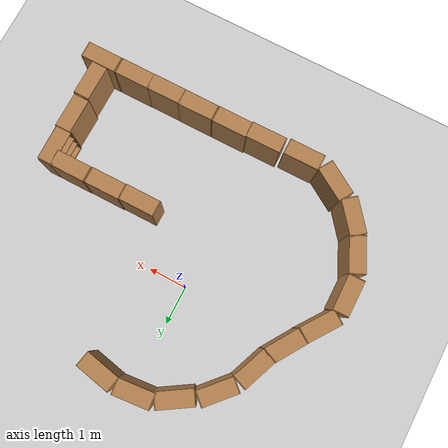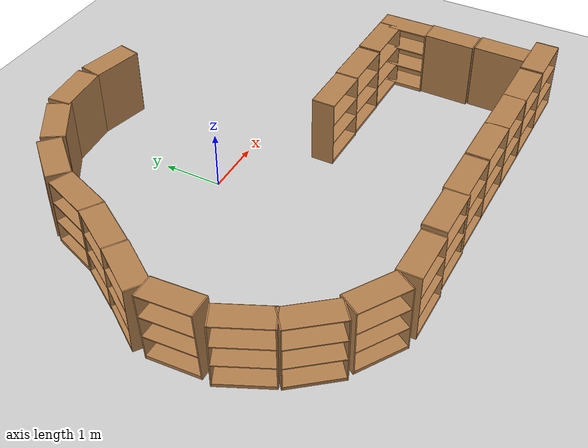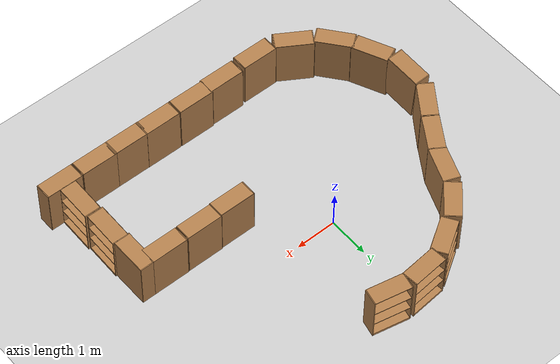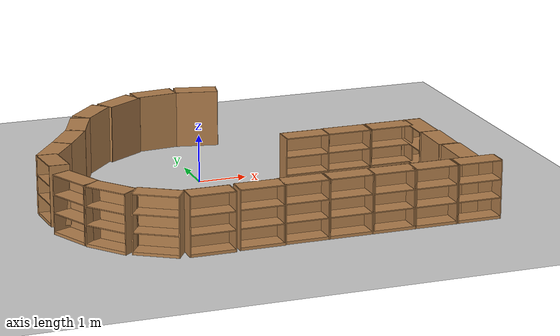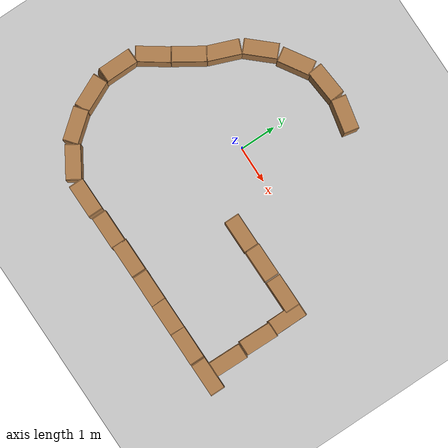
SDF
<sdf version="1.7">
 <world name="default">
  <light name="sun" type="directional">
   <pose>0 0 10 0 -0 0</pose>
   <diffuse>0.8 0.8 0.8 1</diffuse>
   <specular>0.2 0.2 0.2 1</specular>
   <attenuation>
    <range>1000</range>
    <constant>0.9</constant>
    <linear>0.01</linear>
    <quadratic>0.001</quadratic>
   </attenuation>
   <direction>-0.5 0.1 -0.9</direction>
   <spot><inner_angle>0</inner_angle><outer_angle>0</outer_angle><falloff>0</falloff></spot>
  </light>
  <model name="ground_plane">
   <static>1</static>
   <link name="link">
    <collision name="collision">
     <geometry><plane><normal>0 0 1</normal><size>100 100</size></plane></geometry>
     <surface>
      <contact><collide_bitmask>65535</collide_bitmask></contact>
      <friction><ode><mu>100</mu><mu2>50</mu2></ode></friction>
     </surface>
    </collision>
    <visual name="visual">
     <cast_shadows>0</cast_shadows>
     <geometry><plane><normal>0 0 1</normal><size>100 100</size></plane></geometry>
     <material>
      <script><uri>file://media/materials/scripts/gazebo.material</uri><name>Gazebo/Grey</name></script>
     </material>
    </visual>
   </link>
  </model>
  <gravity>0 0 -9.8</gravity>
  <magnetic_field>6e-06 2.3e-05 -4.2e-05</magnetic_field>
  <atmosphere type="adiabatic"/>
  <physics type="ode">
   <max_step_size>0.001</max_step_size>
   <real_time_factor>1</real_time_factor>
   <real_time_update_rate>1000</real_time_update_rate>
  </physics>
  <scene><ambient>0.4 0.4 0.4 1</ambient><background>0.7 0.7 0.7 1</background><shadows>1</shadows></scene>
  <audio><device>default</device></audio>
  <spherical_coordinates>
   <surface_model>EARTH_WGS84</surface_model>
   <latitude_deg>0</latitude_deg>
   <longitude_deg>0</longitude_deg>
   <elevation>0</elevation>
   <heading_deg>0</heading_deg>
  </spherical_coordinates>
  <model name="bookshelf">
   <static>1</static>
   <link name="link">
    <inertial><mass>1</mass></inertial>
    <collision name="back">
     <pose>0 0.005 0.6 0 -0 0</pose>
     <geometry><box><size>0.9 0.01 1.2</size></box></geometry>
    </collision>
    <visual name="visual1">
     <pose>0 0.005 0.6 0 -0 0</pose>
     <geometry><box><size>0.9 0.01 1.2</size></box></geometry>
     <material>
      <script><uri>file://media/materials/scripts/gazebo.material</uri><name>Gazebo/Wood</name></script>
     </material>
    </visual>
    <collision name="left_side">
     <pose>0.45 -0.195 0.6 0 -0 0</pose>
     <geometry><box><size>0.02 0.4 1.2</size></box></geometry>
    </collision>
    <visual name="visual2">
     <pose>0.45 -0.195 0.6 0 -0 0</pose>
     <geometry><box><size>0.02 0.4 1.2</size></box></geometry>
     <material>
      <script><uri>file://media/materials/scripts/gazebo.material</uri><name>Gazebo/Wood</name></script>
     </material>
    </visual>
    <collision name="right_side">
     <pose>-0.45 -0.195 0.6 0 -0 0</pose>
     <geometry><box><size>0.02 0.4 1.2</size></box></geometry>
    </collision>
    <visual name="visual3">
     <pose>-0.45 -0.195 0.6 0 -0 0</pose>
     <geometry><box><size>0.02 0.4 1.2</size></box></geometry>
     <material>
      <script><uri>file://media/materials/scripts/gazebo.material</uri><name>Gazebo/Wood</name></script>
     </material>
    </visual>
    <collision name="bottom">
     <pose>0 -0.195 0.03 0 -0 0</pose>
     <geometry><box><size>0.88 0.4 0.06</size></box></geometry>
    </collision>
    <visual name="visual4">
     <pose>0 -0.195 0.03 0 -0 0</pose>
     <geometry><box><size>0.88 0.4 0.06</size></box></geometry>
     <material>
      <script><uri>file://media/materials/scripts/gazebo.material</uri><name>Gazebo/Wood</name></script>
     </material>
    </visual>
    <collision name="top">
     <pose>0 -0.195 1.19 0 -0 0</pose>
     <geometry><box><size>0.88 0.4 0.02</size></box></geometry>
    </collision>
    <visual name="visual5">
     <pose>0 -0.195 1.19 0 -0 0</pose>
     <geometry><box><size>0.88 0.4 0.02</size></box></geometry>
     <material>
      <script><uri>file://media/materials/scripts/gazebo.material</uri><name>Gazebo/Wood</name></script>
     </material>
    </visual>
    <collision name="low_shelf">
     <pose>0 -0.195 0.43 0 -0 0</pose>
     <geometry><box><size>0.88 0.4 0.02</size></box></geometry>
    </collision>
    <visual name="visual6">
     <pose>0 -0.195 0.43 0 -0 0</pose>
     <geometry><box><size>0.88 0.4 0.02</size></box></geometry>
     <material>
      <script><uri>file://media/materials/scripts/gazebo.material</uri><name>Gazebo/Wood</name></script>
     </material>
    </visual>
    <collision name="high_shelf">
     <pose>0 -0.195 0.8 0 -0 0</pose>
     <geometry><box><size>0.88 0.4 0.02</size></box></geometry>
    </collision>
    <visual name="visual7">
     <pose>0 -0.195 0.8 0 -0 0</pose>
     <geometry><box><size>0.88 0.4 0.02</size></box></geometry>
     <material>
      <script><uri>file://media/materials/scripts/gazebo.material</uri><name>Gazebo/Wood</name></script>
     </material>
    </visual>
   </link>
   <pose>-3.24887 -1.54956 0.088565 -0.012294 -0.060689 -1.55302</pose>
  </model>
  <model name="bookshelf_0">
   <static>1</static>
   <link name="link">
    <inertial><mass>1</mass></inertial>
    <collision name="back">
     <pose>0 0.005 0.6 0 -0 0</pose>
     <geometry><box><size>0.9 0.01 1.2</size></box></geometry>
    </collision>
    <visual name="visual1">
     <pose>0 0.005 0.6 0 -0 0</pose>
     <geometry><box><size>0.9 0.01 1.2</size></box></geometry>
     <material>
      <script><uri>file://media/materials/scripts/gazebo.material</uri><name>Gazebo/Wood</name></script>
     </material>
    </visual>
    <collision name="left_side">
     <pose>0.45 -0.195 0.6 0 -0 0</pose>
     <geometry><box><size>0.02 0.4 1.2</size></box></geometry>
    </collision>
    <visual name="visual2">
     <pose>0.45 -0.195 0.6 0 -0 0</pose>
     <geometry><box><size>0.02 0.4 1.2</size></box></geometry>
     <material>
      <script><uri>file://media/materials/scripts/gazebo.material</uri><name>Gazebo/Wood</name></script>
     </material>
    </visual>
    <collision name="right_side">
     <pose>-0.45 -0.195 0.6 0 -0 0</pose>
     <geometry><box><size>0.02 0.4 1.2</size></box></geometry>
    </collision>
    <visual name="visual3">
     <pose>-0.45 -0.195 0.6 0 -0 0</pose>
     <geometry><box><size>0.02 0.4 1.2</size></box></geometry>
     <material>
      <script><uri>file://media/materials/scripts/gazebo.material</uri><name>Gazebo/Wood</name></script>
     </material>
    </visual>
    <collision name="bottom">
     <pose>0 -0.195 0.03 0 -0 0</pose>
     <geometry><box><size>0.88 0.4 0.06</size></box></geometry>
    </collision>
    <visual name="visual4">
     <pose>0 -0.195 0.03 0 -0 0</pose>
     <geometry><box><size>0.88 0.4 0.06</size></box></geometry>
     <material>
      <script><uri>file://media/materials/scripts/gazebo.material</uri><name>Gazebo/Wood</name></script>
     </material>
    </visual>
    <collision name="top">
     <pose>0 -0.195 1.19 0 -0 0</pose>
     <geometry><box><size>0.88 0.4 0.02</size></box></geometry>
    </collision>
    <visual name="visual5">
     <pose>0 -0.195 1.19 0 -0 0</pose>
     <geometry><box><size>0.88 0.4 0.02</size></box></geometry>
     <material>
      <script><uri>file://media/materials/scripts/gazebo.material</uri><name>Gazebo/Wood</name></script>
     </material>
    </visual>
    <collision name="low_shelf">
     <pose>0 -0.195 0.43 0 -0 0</pose>
     <geometry><box><size>0.88 0.4 0.02</size></box></geometry>
    </collision>
    <visual name="visual6">
     <pose>0 -0.195 0.43 0 -0 0</pose>
     <geometry><box><size>0.88 0.4 0.02</size></box></geometry>
     <material>
      <script><uri>file://media/materials/scripts/gazebo.material</uri><name>Gazebo/Wood</name></script>
     </material>
    </visual>
    <collision name="high_shelf">
     <pose>0 -0.195 0.8 0 -0 0</pose>
     <geometry><box><size>0.88 0.4 0.02</size></box></geometry>
    </collision>
    <visual name="visual7">
     <pose>0 -0.195 0.8 0 -0 0</pose>
     <geometry><box><size>0.88 0.4 0.02</size></box></geometry>
     <material>
      <script><uri>file://media/materials/scripts/gazebo.material</uri><name>Gazebo/Wood</name></script>
     </material>
    </visual>
   </link>
   <pose>-2.61978 -3.08808 0 0 0 -0.896017</pose>
  </model>
  <model name="bookshelf_1">
   <static>1</static>
   <link name="link">
    <inertial><mass>1</mass></inertial>
    <collision name="back">
     <pose>0 0.005 0.6 0 -0 0</pose>
     <geometry><box><size>0.9 0.01 1.2</size></box></geometry>
    </collision>
    <visual name="visual1">
     <pose>0 0.005 0.6 0 -0 0</pose>
     <geometry><box><size>0.9 0.01 1.2</size></box></geometry>
     <material>
      <script><uri>file://media/materials/scripts/gazebo.material</uri><name>Gazebo/Wood</name></script>
     </material>
    </visual>
    <collision name="left_side">
     <pose>0.45 -0.195 0.6 0 -0 0</pose>
     <geometry><box><size>0.02 0.4 1.2</size></box></geometry>
    </collision>
    <visual name="visual2">
     <pose>0.45 -0.195 0.6 0 -0 0</pose>
     <geometry><box><size>0.02 0.4 1.2</size></box></geometry>
     <material>
      <script><uri>file://media/materials/scripts/gazebo.material</uri><name>Gazebo/Wood</name></script>
     </material>
    </visual>
    <collision name="right_side">
     <pose>-0.45 -0.195 0.6 0 -0 0</pose>
     <geometry><box><size>0.02 0.4 1.2</size></box></geometry>
    </collision>
    <visual name="visual3">
     <pose>-0.45 -0.195 0.6 0 -0 0</pose>
     <geometry><box><size>0.02 0.4 1.2</size></box></geometry>
     <material>
      <script><uri>file://media/materials/scripts/gazebo.material</uri><name>Gazebo/Wood</name></script>
     </material>
    </visual>
    <collision name="bottom">
     <pose>0 -0.195 0.03 0 -0 0</pose>
     <geometry><box><size>0.88 0.4 0.06</size></box></geometry>
    </collision>
    <visual name="visual4">
     <pose>0 -0.195 0.03 0 -0 0</pose>
     <geometry><box><size>0.88 0.4 0.06</size></box></geometry>
     <material>
      <script><uri>file://media/materials/scripts/gazebo.material</uri><name>Gazebo/Wood</name></script>
     </material>
    </visual>
    <collision name="top">
     <pose>0 -0.195 1.19 0 -0 0</pose>
     <geometry><box><size>0.88 0.4 0.02</size></box></geometry>
    </collision>
    <visual name="visual5">
     <pose>0 -0.195 1.19 0 -0 0</pose>
     <geometry><box><size>0.88 0.4 0.02</size></box></geometry>
     <material>
      <script><uri>file://media/materials/scripts/gazebo.material</uri><name>Gazebo/Wood</name></script>
     </material>
    </visual>
    <collision name="low_shelf">
     <pose>0 -0.195 0.43 0 -0 0</pose>
     <geometry><box><size>0.88 0.4 0.02</size></box></geometry>
    </collision>
    <visual name="visual6">
     <pose>0 -0.195 0.43 0 -0 0</pose>
     <geometry><box><size>0.88 0.4 0.02</size></box></geometry>
     <material>
      <script><uri>file://media/materials/scripts/gazebo.material</uri><name>Gazebo/Wood</name></script>
     </material>
    </visual>
    <collision name="high_shelf">
     <pose>0 -0.195 0.8 0 -0 0</pose>
     <geometry><box><size>0.88 0.4 0.02</size></box></geometry>
    </collision>
    <visual name="visual7">
     <pose>0 -0.195 0.8 0 -0 0</pose>
     <geometry><box><size>0.88 0.4 0.02</size></box></geometry>
     <material>
      <script><uri>file://media/materials/scripts/gazebo.material</uri><name>Gazebo/Wood</name></script>
     </material>
    </visual>
   </link>
   <pose>-1.92809 -3.61462 0 0 0 -0.558272</pose>
  </model>
  <model name="bookshelf_2">
   <static>1</static>
   <link name="link">
    <inertial><mass>1</mass></inertial>
    <collision name="back">
     <pose>0 0.005 0.6 0 -0 0</pose>
     <geometry><box><size>0.9 0.01 1.2</size></box></geometry>
    </collision>
    <visual name="visual1">
     <pose>0 0.005 0.6 0 -0 0</pose>
     <geometry><box><size>0.9 0.01 1.2</size></box></geometry>
     <material>
      <script><uri>file://media/materials/scripts/gazebo.material</uri><name>Gazebo/Wood</name></script>
     </material>
    </visual>
    <collision name="left_side">
     <pose>0.45 -0.195 0.6 0 -0 0</pose>
     <geometry><box><size>0.02 0.4 1.2</size></box></geometry>
    </collision>
    <visual name="visual2">
     <pose>0.45 -0.195 0.6 0 -0 0</pose>
     <geometry><box><size>0.02 0.4 1.2</size></box></geometry>
     <material>
      <script><uri>file://media/materials/scripts/gazebo.material</uri><name>Gazebo/Wood</name></script>
     </material>
    </visual>
    <collision name="right_side">
     <pose>-0.45 -0.195 0.6 0 -0 0</pose>
     <geometry><box><size>0.02 0.4 1.2</size></box></geometry>
    </collision>
    <visual name="visual3">
     <pose>-0.45 -0.195 0.6 0 -0 0</pose>
     <geometry><box><size>0.02 0.4 1.2</size></box></geometry>
     <material>
      <script><uri>file://media/materials/scripts/gazebo.material</uri><name>Gazebo/Wood</name></script>
     </material>
    </visual>
    <collision name="bottom">
     <pose>0 -0.195 0.03 0 -0 0</pose>
     <geometry><box><size>0.88 0.4 0.06</size></box></geometry>
    </collision>
    <visual name="visual4">
     <pose>0 -0.195 0.03 0 -0 0</pose>
     <geometry><box><size>0.88 0.4 0.06</size></box></geometry>
     <material>
      <script><uri>file://media/materials/scripts/gazebo.material</uri><name>Gazebo/Wood</name></script>
     </material>
    </visual>
    <collision name="top">
     <pose>0 -0.195 1.19 0 -0 0</pose>
     <geometry><box><size>0.88 0.4 0.02</size></box></geometry>
    </collision>
    <visual name="visual5">
     <pose>0 -0.195 1.19 0 -0 0</pose>
     <geometry><box><size>0.88 0.4 0.02</size></box></geometry>
     <material>
      <script><uri>file://media/materials/scripts/gazebo.material</uri><name>Gazebo/Wood</name></script>
     </material>
    </visual>
    <collision name="low_shelf">
     <pose>0 -0.195 0.43 0 -0 0</pose>
     <geometry><box><size>0.88 0.4 0.02</size></box></geometry>
    </collision>
    <visual name="visual6">
     <pose>0 -0.195 0.43 0 -0 0</pose>
     <geometry><box><size>0.88 0.4 0.02</size></box></geometry>
     <material>
      <script><uri>file://media/materials/scripts/gazebo.material</uri><name>Gazebo/Wood</name></script>
     </material>
    </visual>
    <collision name="high_shelf">
     <pose>0 -0.195 0.8 0 -0 0</pose>
     <geometry><box><size>0.88 0.4 0.02</size></box></geometry>
    </collision>
    <visual name="visual7">
     <pose>0 -0.195 0.8 0 -0 0</pose>
     <geometry><box><size>0.88 0.4 0.02</size></box></geometry>
     <material>
      <script><uri>file://media/materials/scripts/gazebo.material</uri><name>Gazebo/Wood</name></script>
     </material>
    </visual>
   </link>
   <pose>-1.10045 -3.82042 0 0 -0 0</pose>
  </model>
  <model name="bookshelf_3">
   <static>1</static>
   <link name="link">
    <inertial><mass>1</mass></inertial>
    <collision name="back">
     <pose>0 0.005 0.6 0 -0 0</pose>
     <geometry><box><size>0.9 0.01 1.2</size></box></geometry>
    </collision>
    <visual name="visual1">
     <pose>0 0.005 0.6 0 -0 0</pose>
     <geometry><box><size>0.9 0.01 1.2</size></box></geometry>
     <material>
      <script><uri>file://media/materials/scripts/gazebo.material</uri><name>Gazebo/Wood</name></script>
     </material>
    </visual>
    <collision name="left_side">
     <pose>0.45 -0.195 0.6 0 -0 0</pose>
     <geometry><box><size>0.02 0.4 1.2</size></box></geometry>
    </collision>
    <visual name="visual2">
     <pose>0.45 -0.195 0.6 0 -0 0</pose>
     <geometry><box><size>0.02 0.4 1.2</size></box></geometry>
     <material>
      <script><uri>file://media/materials/scripts/gazebo.material</uri><name>Gazebo/Wood</name></script>
     </material>
    </visual>
    <collision name="right_side">
     <pose>-0.45 -0.195 0.6 0 -0 0</pose>
     <geometry><box><size>0.02 0.4 1.2</size></box></geometry>
    </collision>
    <visual name="visual3">
     <pose>-0.45 -0.195 0.6 0 -0 0</pose>
     <geometry><box><size>0.02 0.4 1.2</size></box></geometry>
     <material>
      <script><uri>file://media/materials/scripts/gazebo.material</uri><name>Gazebo/Wood</name></script>
     </material>
    </visual>
    <collision name="bottom">
     <pose>0 -0.195 0.03 0 -0 0</pose>
     <geometry><box><size>0.88 0.4 0.06</size></box></geometry>
    </collision>
    <visual name="visual4">
     <pose>0 -0.195 0.03 0 -0 0</pose>
     <geometry><box><size>0.88 0.4 0.06</size></box></geometry>
     <material>
      <script><uri>file://media/materials/scripts/gazebo.material</uri><name>Gazebo/Wood</name></script>
     </material>
    </visual>
    <collision name="top">
     <pose>0 -0.195 1.19 0 -0 0</pose>
     <geometry><box><size>0.88 0.4 0.02</size></box></geometry>
    </collision>
    <visual name="visual5">
     <pose>0 -0.195 1.19 0 -0 0</pose>
     <geometry><box><size>0.88 0.4 0.02</size></box></geometry>
     <material>
      <script><uri>file://media/materials/scripts/gazebo.material</uri><name>Gazebo/Wood</name></script>
     </material>
    </visual>
    <collision name="low_shelf">
     <pose>0 -0.195 0.43 0 -0 0</pose>
     <geometry><box><size>0.88 0.4 0.02</size></box></geometry>
    </collision>
    <visual name="visual6">
     <pose>0 -0.195 0.43 0 -0 0</pose>
     <geometry><box><size>0.88 0.4 0.02</size></box></geometry>
     <material>
      <script><uri>file://media/materials/scripts/gazebo.material</uri><name>Gazebo/Wood</name></script>
     </material>
    </visual>
    <collision name="high_shelf">
     <pose>0 -0.195 0.8 0 -0 0</pose>
     <geometry><box><size>0.88 0.4 0.02</size></box></geometry>
    </collision>
    <visual name="visual7">
     <pose>0 -0.195 0.8 0 -0 0</pose>
     <geometry><box><size>0.88 0.4 0.02</size></box></geometry>
     <material>
      <script><uri>file://media/materials/scripts/gazebo.material</uri><name>Gazebo/Wood</name></script>
     </material>
    </visual>
   </link>
   <pose>-0.108426 -3.78195 0 0 -0 0</pose>
  </model>
  <model name="bookshelf_4">
   <static>1</static>
   <link name="link">
    <inertial><mass>1</mass></inertial>
    <collision name="back">
     <pose>0 0.005 0.6 0 -0 0</pose>
     <geometry><box><size>0.9 0.01 1.2</size></box></geometry>
    </collision>
    <visual name="visual1">
     <pose>0 0.005 0.6 0 -0 0</pose>
     <geometry><box><size>0.9 0.01 1.2</size></box></geometry>
     <material>
      <script><uri>file://media/materials/scripts/gazebo.material</uri><name>Gazebo/Wood</name></script>
     </material>
    </visual>
    <collision name="left_side">
     <pose>0.45 -0.195 0.6 0 -0 0</pose>
     <geometry><box><size>0.02 0.4 1.2</size></box></geometry>
    </collision>
    <visual name="visual2">
     <pose>0.45 -0.195 0.6 0 -0 0</pose>
     <geometry><box><size>0.02 0.4 1.2</size></box></geometry>
     <material>
      <script><uri>file://media/materials/scripts/gazebo.material</uri><name>Gazebo/Wood</name></script>
     </material>
    </visual>
    <collision name="right_side">
     <pose>-0.45 -0.195 0.6 0 -0 0</pose>
     <geometry><box><size>0.02 0.4 1.2</size></box></geometry>
    </collision>
    <visual name="visual3">
     <pose>-0.45 -0.195 0.6 0 -0 0</pose>
     <geometry><box><size>0.02 0.4 1.2</size></box></geometry>
     <material>
      <script><uri>file://media/materials/scripts/gazebo.material</uri><name>Gazebo/Wood</name></script>
     </material>
    </visual>
    <collision name="bottom">
     <pose>0 -0.195 0.03 0 -0 0</pose>
     <geometry><box><size>0.88 0.4 0.06</size></box></geometry>
    </collision>
    <visual name="visual4">
     <pose>0 -0.195 0.03 0 -0 0</pose>
     <geometry><box><size>0.88 0.4 0.06</size></box></geometry>
     <material>
      <script><uri>file://media/materials/scripts/gazebo.material</uri><name>Gazebo/Wood</name></script>
     </material>
    </visual>
    <collision name="top">
     <pose>0 -0.195 1.19 0 -0 0</pose>
     <geometry><box><size>0.88 0.4 0.02</size></box></geometry>
    </collision>
    <visual name="visual5">
     <pose>0 -0.195 1.19 0 -0 0</pose>
     <geometry><box><size>0.88 0.4 0.02</size></box></geometry>
     <material>
      <script><uri>file://media/materials/scripts/gazebo.material</uri><name>Gazebo/Wood</name></script>
     </material>
    </visual>
    <collision name="low_shelf">
     <pose>0 -0.195 0.43 0 -0 0</pose>
     <geometry><box><size>0.88 0.4 0.02</size></box></geometry>
    </collision>
    <visual name="visual6">
     <pose>0 -0.195 0.43 0 -0 0</pose>
     <geometry><box><size>0.88 0.4 0.02</size></box></geometry>
     <material>
      <script><uri>file://media/materials/scripts/gazebo.material</uri><name>Gazebo/Wood</name></script>
     </material>
    </visual>
    <collision name="high_shelf">
     <pose>0 -0.195 0.8 0 -0 0</pose>
     <geometry><box><size>0.88 0.4 0.02</size></box></geometry>
    </collision>
    <visual name="visual7">
     <pose>0 -0.195 0.8 0 -0 0</pose>
     <geometry><box><size>0.88 0.4 0.02</size></box></geometry>
     <material>
      <script><uri>file://media/materials/scripts/gazebo.material</uri><name>Gazebo/Wood</name></script>
     </material>
    </visual>
   </link>
   <pose>0.772368 -3.75609 0 0 -0 0</pose>
  </model>
  <model name="bookshelf_5">
   <static>1</static>
   <link name="link">
    <inertial><mass>1</mass></inertial>
    <collision name="back">
     <pose>0 0.005 0.6 0 -0 0</pose>
     <geometry><box><size>0.9 0.01 1.2</size></box></geometry>
    </collision>
    <visual name="visual1">
     <pose>0 0.005 0.6 0 -0 0</pose>
     <geometry><box><size>0.9 0.01 1.2</size></box></geometry>
     <material>
      <script><uri>file://media/materials/scripts/gazebo.material</uri><name>Gazebo/Wood</name></script>
     </material>
    </visual>
    <collision name="left_side">
     <pose>0.45 -0.195 0.6 0 -0 0</pose>
     <geometry><box><size>0.02 0.4 1.2</size></box></geometry>
    </collision>
    <visual name="visual2">
     <pose>0.45 -0.195 0.6 0 -0 0</pose>
     <geometry><box><size>0.02 0.4 1.2</size></box></geometry>
     <material>
      <script><uri>file://media/materials/scripts/gazebo.material</uri><name>Gazebo/Wood</name></script>
     </material>
    </visual>
    <collision name="right_side">
     <pose>-0.45 -0.195 0.6 0 -0 0</pose>
     <geometry><box><size>0.02 0.4 1.2</size></box></geometry>
    </collision>
    <visual name="visual3">
     <pose>-0.45 -0.195 0.6 0 -0 0</pose>
     <geometry><box><size>0.02 0.4 1.2</size></box></geometry>
     <material>
      <script><uri>file://media/materials/scripts/gazebo.material</uri><name>Gazebo/Wood</name></script>
     </material>
    </visual>
    <collision name="bottom">
     <pose>0 -0.195 0.03 0 -0 0</pose>
     <geometry><box><size>0.88 0.4 0.06</size></box></geometry>
    </collision>
    <visual name="visual4">
     <pose>0 -0.195 0.03 0 -0 0</pose>
     <geometry><box><size>0.88 0.4 0.06</size></box></geometry>
     <material>
      <script><uri>file://media/materials/scripts/gazebo.material</uri><name>Gazebo/Wood</name></script>
     </material>
    </visual>
    <collision name="top">
     <pose>0 -0.195 1.19 0 -0 0</pose>
     <geometry><box><size>0.88 0.4 0.02</size></box></geometry>
    </collision>
    <visual name="visual5">
     <pose>0 -0.195 1.19 0 -0 0</pose>
     <geometry><box><size>0.88 0.4 0.02</size></box></geometry>
     <material>
      <script><uri>file://media/materials/scripts/gazebo.material</uri><name>Gazebo/Wood</name></script>
     </material>
    </visual>
    <collision name="low_shelf">
     <pose>0 -0.195 0.43 0 -0 0</pose>
     <geometry><box><size>0.88 0.4 0.02</size></box></geometry>
    </collision>
    <visual name="visual6">
     <pose>0 -0.195 0.43 0 -0 0</pose>
     <geometry><box><size>0.88 0.4 0.02</size></box></geometry>
     <material>
      <script><uri>file://media/materials/scripts/gazebo.material</uri><name>Gazebo/Wood</name></script>
     </material>
    </visual>
    <collision name="high_shelf">
     <pose>0 -0.195 0.8 0 -0 0</pose>
     <geometry><box><size>0.88 0.4 0.02</size></box></geometry>
    </collision>
    <visual name="visual7">
     <pose>0 -0.195 0.8 0 -0 0</pose>
     <geometry><box><size>0.88 0.4 0.02</size></box></geometry>
     <material>
      <script><uri>file://media/materials/scripts/gazebo.material</uri><name>Gazebo/Wood</name></script>
     </material>
    </visual>
   </link>
   <pose>1.6996 -3.75399 0 0 -0 0</pose>
  </model>
  <model name="bookshelf_6">
   <static>1</static>
   <link name="link">
    <inertial><mass>1</mass></inertial>
    <collision name="back">
     <pose>0 0.005 0.6 0 -0 0</pose>
     <geometry><box><size>0.9 0.01 1.2</size></box></geometry>
    </collision>
    <visual name="visual1">
     <pose>0 0.005 0.6 0 -0 0</pose>
     <geometry><box><size>0.9 0.01 1.2</size></box></geometry>
     <material>
      <script><uri>file://media/materials/scripts/gazebo.material</uri><name>Gazebo/Wood</name></script>
     </material>
    </visual>
    <collision name="left_side">
     <pose>0.45 -0.195 0.6 0 -0 0</pose>
     <geometry><box><size>0.02 0.4 1.2</size></box></geometry>
    </collision>
    <visual name="visual2">
     <pose>0.45 -0.195 0.6 0 -0 0</pose>
     <geometry><box><size>0.02 0.4 1.2</size></box></geometry>
     <material>
      <script><uri>file://media/materials/scripts/gazebo.material</uri><name>Gazebo/Wood</name></script>
     </material>
    </visual>
    <collision name="right_side">
     <pose>-0.45 -0.195 0.6 0 -0 0</pose>
     <geometry><box><size>0.02 0.4 1.2</size></box></geometry>
    </collision>
    <visual name="visual3">
     <pose>-0.45 -0.195 0.6 0 -0 0</pose>
     <geometry><box><size>0.02 0.4 1.2</size></box></geometry>
     <material>
      <script><uri>file://media/materials/scripts/gazebo.material</uri><name>Gazebo/Wood</name></script>
     </material>
    </visual>
    <collision name="bottom">
     <pose>0 -0.195 0.03 0 -0 0</pose>
     <geometry><box><size>0.88 0.4 0.06</size></box></geometry>
    </collision>
    <visual name="visual4">
     <pose>0 -0.195 0.03 0 -0 0</pose>
     <geometry><box><size>0.88 0.4 0.06</size></box></geometry>
     <material>
      <script><uri>file://media/materials/scripts/gazebo.material</uri><name>Gazebo/Wood</name></script>
     </material>
    </visual>
    <collision name="top">
     <pose>0 -0.195 1.19 0 -0 0</pose>
     <geometry><box><size>0.88 0.4 0.02</size></box></geometry>
    </collision>
    <visual name="visual5">
     <pose>0 -0.195 1.19 0 -0 0</pose>
     <geometry><box><size>0.88 0.4 0.02</size></box></geometry>
     <material>
      <script><uri>file://media/materials/scripts/gazebo.material</uri><name>Gazebo/Wood</name></script>
     </material>
    </visual>
    <collision name="low_shelf">
     <pose>0 -0.195 0.43 0 -0 0</pose>
     <geometry><box><size>0.88 0.4 0.02</size></box></geometry>
    </collision>
    <visual name="visual6">
     <pose>0 -0.195 0.43 0 -0 0</pose>
     <geometry><box><size>0.88 0.4 0.02</size></box></geometry>
     <material>
      <script><uri>file://media/materials/scripts/gazebo.material</uri><name>Gazebo/Wood</name></script>
     </material>
    </visual>
    <collision name="high_shelf">
     <pose>0 -0.195 0.8 0 -0 0</pose>
     <geometry><box><size>0.88 0.4 0.02</size></box></geometry>
    </collision>
    <visual name="visual7">
     <pose>0 -0.195 0.8 0 -0 0</pose>
     <geometry><box><size>0.88 0.4 0.02</size></box></geometry>
     <material>
      <script><uri>file://media/materials/scripts/gazebo.material</uri><name>Gazebo/Wood</name></script>
     </material>
    </visual>
   </link>
   <pose>1.82439 -1.04453 0 0 -0 0</pose>
  </model>
  <model name="bookshelf_7">
   <static>1</static>
   <link name="link">
    <inertial><mass>1</mass></inertial>
    <collision name="back">
     <pose>0 0.005 0.6 0 -0 0</pose>
     <geometry><box><size>0.9 0.01 1.2</size></box></geometry>
    </collision>
    <visual name="visual1">
     <pose>0 0.005 0.6 0 -0 0</pose>
     <geometry><box><size>0.9 0.01 1.2</size></box></geometry>
     <material>
      <script><uri>file://media/materials/scripts/gazebo.material</uri><name>Gazebo/Wood</name></script>
     </material>
    </visual>
    <collision name="left_side">
     <pose>0.45 -0.195 0.6 0 -0 0</pose>
     <geometry><box><size>0.02 0.4 1.2</size></box></geometry>
    </collision>
    <visual name="visual2">
     <pose>0.45 -0.195 0.6 0 -0 0</pose>
     <geometry><box><size>0.02 0.4 1.2</size></box></geometry>
     <material>
      <script><uri>file://media/materials/scripts/gazebo.material</uri><name>Gazebo/Wood</name></script>
     </material>
    </visual>
    <collision name="right_side">
     <pose>-0.45 -0.195 0.6 0 -0 0</pose>
     <geometry><box><size>0.02 0.4 1.2</size></box></geometry>
    </collision>
    <visual name="visual3">
     <pose>-0.45 -0.195 0.6 0 -0 0</pose>
     <geometry><box><size>0.02 0.4 1.2</size></box></geometry>
     <material>
      <script><uri>file://media/materials/scripts/gazebo.material</uri><name>Gazebo/Wood</name></script>
     </material>
    </visual>
    <collision name="bottom">
     <pose>0 -0.195 0.03 0 -0 0</pose>
     <geometry><box><size>0.88 0.4 0.06</size></box></geometry>
    </collision>
    <visual name="visual4">
     <pose>0 -0.195 0.03 0 -0 0</pose>
     <geometry><box><size>0.88 0.4 0.06</size></box></geometry>
     <material>
      <script><uri>file://media/materials/scripts/gazebo.material</uri><name>Gazebo/Wood</name></script>
     </material>
    </visual>
    <collision name="top">
     <pose>0 -0.195 1.19 0 -0 0</pose>
     <geometry><box><size>0.88 0.4 0.02</size></box></geometry>
    </collision>
    <visual name="visual5">
     <pose>0 -0.195 1.19 0 -0 0</pose>
     <geometry><box><size>0.88 0.4 0.02</size></box></geometry>
     <material>
      <script><uri>file://media/materials/scripts/gazebo.material</uri><name>Gazebo/Wood</name></script>
     </material>
    </visual>
    <collision name="low_shelf">
     <pose>0 -0.195 0.43 0 -0 0</pose>
     <geometry><box><size>0.88 0.4 0.02</size></box></geometry>
    </collision>
    <visual name="visual6">
     <pose>0 -0.195 0.43 0 -0 0</pose>
     <geometry><box><size>0.88 0.4 0.02</size></box></geometry>
     <material>
      <script><uri>file://media/materials/scripts/gazebo.material</uri><name>Gazebo/Wood</name></script>
     </material>
    </visual>
    <collision name="high_shelf">
     <pose>0 -0.195 0.8 0 -0 0</pose>
     <geometry><box><size>0.88 0.4 0.02</size></box></geometry>
    </collision>
    <visual name="visual7">
     <pose>0 -0.195 0.8 0 -0 0</pose>
     <geometry><box><size>0.88 0.4 0.02</size></box></geometry>
     <material>
      <script><uri>file://media/materials/scripts/gazebo.material</uri><name>Gazebo/Wood</name></script>
     </material>
    </visual>
   </link>
   <pose>2.56274 -3.75756 0 0 -0 0</pose>
  </model>
  <model name="bookshelf_8">
   <static>1</static>
   <link name="link">
    <inertial><mass>1</mass></inertial>
    <collision name="back">
     <pose>0 0.005 0.6 0 -0 0</pose>
     <geometry><box><size>0.9 0.01 1.2</size></box></geometry>
    </collision>
    <visual name="visual1">
     <pose>0 0.005 0.6 0 -0 0</pose>
     <geometry><box><size>0.9 0.01 1.2</size></box></geometry>
     <material>
      <script><uri>file://media/materials/scripts/gazebo.material</uri><name>Gazebo/Wood</name></script>
     </material>
    </visual>
    <collision name="left_side">
     <pose>0.45 -0.195 0.6 0 -0 0</pose>
     <geometry><box><size>0.02 0.4 1.2</size></box></geometry>
    </collision>
    <visual name="visual2">
     <pose>0.45 -0.195 0.6 0 -0 0</pose>
     <geometry><box><size>0.02 0.4 1.2</size></box></geometry>
     <material>
      <script><uri>file://media/materials/scripts/gazebo.material</uri><name>Gazebo/Wood</name></script>
     </material>
    </visual>
    <collision name="right_side">
     <pose>-0.45 -0.195 0.6 0 -0 0</pose>
     <geometry><box><size>0.02 0.4 1.2</size></box></geometry>
    </collision>
    <visual name="visual3">
     <pose>-0.45 -0.195 0.6 0 -0 0</pose>
     <geometry><box><size>0.02 0.4 1.2</size></box></geometry>
     <material>
      <script><uri>file://media/materials/scripts/gazebo.material</uri><name>Gazebo/Wood</name></script>
     </material>
    </visual>
    <collision name="bottom">
     <pose>0 -0.195 0.03 0 -0 0</pose>
     <geometry><box><size>0.88 0.4 0.06</size></box></geometry>
    </collision>
    <visual name="visual4">
     <pose>0 -0.195 0.03 0 -0 0</pose>
     <geometry><box><size>0.88 0.4 0.06</size></box></geometry>
     <material>
      <script><uri>file://media/materials/scripts/gazebo.material</uri><name>Gazebo/Wood</name></script>
     </material>
    </visual>
    <collision name="top">
     <pose>0 -0.195 1.19 0 -0 0</pose>
     <geometry><box><size>0.88 0.4 0.02</size></box></geometry>
    </collision>
    <visual name="visual5">
     <pose>0 -0.195 1.19 0 -0 0</pose>
     <geometry><box><size>0.88 0.4 0.02</size></box></geometry>
     <material>
      <script><uri>file://media/materials/scripts/gazebo.material</uri><name>Gazebo/Wood</name></script>
     </material>
    </visual>
    <collision name="low_shelf">
     <pose>0 -0.195 0.43 0 -0 0</pose>
     <geometry><box><size>0.88 0.4 0.02</size></box></geometry>
    </collision>
    <visual name="visual6">
     <pose>0 -0.195 0.43 0 -0 0</pose>
     <geometry><box><size>0.88 0.4 0.02</size></box></geometry>
     <material>
      <script><uri>file://media/materials/scripts/gazebo.material</uri><name>Gazebo/Wood</name></script>
     </material>
    </visual>
    <collision name="high_shelf">
     <pose>0 -0.195 0.8 0 -0 0</pose>
     <geometry><box><size>0.88 0.4 0.02</size></box></geometry>
    </collision>
    <visual name="visual7">
     <pose>0 -0.195 0.8 0 -0 0</pose>
     <geometry><box><size>0.88 0.4 0.02</size></box></geometry>
     <material>
      <script><uri>file://media/materials/scripts/gazebo.material</uri><name>Gazebo/Wood</name></script>
     </material>
    </visual>
   </link>
   <pose>2.73157 -1.02877 0 0 -0 0</pose>
  </model>
  <model name="bookshelf_9">
   <static>1</static>
   <link name="link">
    <inertial><mass>1</mass></inertial>
    <collision name="back">
     <pose>0 0.005 0.6 0 -0 0</pose>
     <geometry><box><size>0.9 0.01 1.2</size></box></geometry>
    </collision>
    <visual name="visual1">
     <pose>0 0.005 0.6 0 -0 0</pose>
     <geometry><box><size>0.9 0.01 1.2</size></box></geometry>
     <material>
      <script><uri>file://media/materials/scripts/gazebo.material</uri><name>Gazebo/Wood</name></script>
     </material>
    </visual>
    <collision name="left_side">
     <pose>0.45 -0.195 0.6 0 -0 0</pose>
     <geometry><box><size>0.02 0.4 1.2</size></box></geometry>
    </collision>
    <visual name="visual2">
     <pose>0.45 -0.195 0.6 0 -0 0</pose>
     <geometry><box><size>0.02 0.4 1.2</size></box></geometry>
     <material>
      <script><uri>file://media/materials/scripts/gazebo.material</uri><name>Gazebo/Wood</name></script>
     </material>
    </visual>
    <collision name="right_side">
     <pose>-0.45 -0.195 0.6 0 -0 0</pose>
     <geometry><box><size>0.02 0.4 1.2</size></box></geometry>
    </collision>
    <visual name="visual3">
     <pose>-0.45 -0.195 0.6 0 -0 0</pose>
     <geometry><box><size>0.02 0.4 1.2</size></box></geometry>
     <material>
      <script><uri>file://media/materials/scripts/gazebo.material</uri><name>Gazebo/Wood</name></script>
     </material>
    </visual>
    <collision name="bottom">
     <pose>0 -0.195 0.03 0 -0 0</pose>
     <geometry><box><size>0.88 0.4 0.06</size></box></geometry>
    </collision>
    <visual name="visual4">
     <pose>0 -0.195 0.03 0 -0 0</pose>
     <geometry><box><size>0.88 0.4 0.06</size></box></geometry>
     <material>
      <script><uri>file://media/materials/scripts/gazebo.material</uri><name>Gazebo/Wood</name></script>
     </material>
    </visual>
    <collision name="top">
     <pose>0 -0.195 1.19 0 -0 0</pose>
     <geometry><box><size>0.88 0.4 0.02</size></box></geometry>
    </collision>
    <visual name="visual5">
     <pose>0 -0.195 1.19 0 -0 0</pose>
     <geometry><box><size>0.88 0.4 0.02</size></box></geometry>
     <material>
      <script><uri>file://media/materials/scripts/gazebo.material</uri><name>Gazebo/Wood</name></script>
     </material>
    </visual>
    <collision name="low_shelf">
     <pose>0 -0.195 0.43 0 -0 0</pose>
     <geometry><box><size>0.88 0.4 0.02</size></box></geometry>
    </collision>
    <visual name="visual6">
     <pose>0 -0.195 0.43 0 -0 0</pose>
     <geometry><box><size>0.88 0.4 0.02</size></box></geometry>
     <material>
      <script><uri>file://media/materials/scripts/gazebo.material</uri><name>Gazebo/Wood</name></script>
     </material>
    </visual>
    <collision name="high_shelf">
     <pose>0 -0.195 0.8 0 -0 0</pose>
     <geometry><box><size>0.88 0.4 0.02</size></box></geometry>
    </collision>
    <visual name="visual7">
     <pose>0 -0.195 0.8 0 -0 0</pose>
     <geometry><box><size>0.88 0.4 0.02</size></box></geometry>
     <material>
      <script><uri>file://media/materials/scripts/gazebo.material</uri><name>Gazebo/Wood</name></script>
     </material>
    </visual>
   </link>
   <pose>3.42347 -3.75551 0 0 -0 0</pose>
  </model>
  <model name="bookshelf_10">
   <static>1</static>
   <link name="link">
    <inertial><mass>1</mass></inertial>
    <collision name="back">
     <pose>0 0.005 0.6 0 -0 0</pose>
     <geometry><box><size>0.9 0.01 1.2</size></box></geometry>
    </collision>
    <visual name="visual1">
     <pose>0 0.005 0.6 0 -0 0</pose>
     <geometry><box><size>0.9 0.01 1.2</size></box></geometry>
     <material>
      <script><uri>file://media/materials/scripts/gazebo.material</uri><name>Gazebo/Wood</name></script>
     </material>
    </visual>
    <collision name="left_side">
     <pose>0.45 -0.195 0.6 0 -0 0</pose>
     <geometry><box><size>0.02 0.4 1.2</size></box></geometry>
    </collision>
    <visual name="visual2">
     <pose>0.45 -0.195 0.6 0 -0 0</pose>
     <geometry><box><size>0.02 0.4 1.2</size></box></geometry>
     <material>
      <script><uri>file://media/materials/scripts/gazebo.material</uri><name>Gazebo/Wood</name></script>
     </material>
    </visual>
    <collision name="right_side">
     <pose>-0.45 -0.195 0.6 0 -0 0</pose>
     <geometry><box><size>0.02 0.4 1.2</size></box></geometry>
    </collision>
    <visual name="visual3">
     <pose>-0.45 -0.195 0.6 0 -0 0</pose>
     <geometry><box><size>0.02 0.4 1.2</size></box></geometry>
     <material>
      <script><uri>file://media/materials/scripts/gazebo.material</uri><name>Gazebo/Wood</name></script>
     </material>
    </visual>
    <collision name="bottom">
     <pose>0 -0.195 0.03 0 -0 0</pose>
     <geometry><box><size>0.88 0.4 0.06</size></box></geometry>
    </collision>
    <visual name="visual4">
     <pose>0 -0.195 0.03 0 -0 0</pose>
     <geometry><box><size>0.88 0.4 0.06</size></box></geometry>
     <material>
      <script><uri>file://media/materials/scripts/gazebo.material</uri><name>Gazebo/Wood</name></script>
     </material>
    </visual>
    <collision name="top">
     <pose>0 -0.195 1.19 0 -0 0</pose>
     <geometry><box><size>0.88 0.4 0.02</size></box></geometry>
    </collision>
    <visual name="visual5">
     <pose>0 -0.195 1.19 0 -0 0</pose>
     <geometry><box><size>0.88 0.4 0.02</size></box></geometry>
     <material>
      <script><uri>file://media/materials/scripts/gazebo.material</uri><name>Gazebo/Wood</name></script>
     </material>
    </visual>
    <collision name="low_shelf">
     <pose>0 -0.195 0.43 0 -0 0</pose>
     <geometry><box><size>0.88 0.4 0.02</size></box></geometry>
    </collision>
    <visual name="visual6">
     <pose>0 -0.195 0.43 0 -0 0</pose>
     <geometry><box><size>0.88 0.4 0.02</size></box></geometry>
     <material>
      <script><uri>file://media/materials/scripts/gazebo.material</uri><name>Gazebo/Wood</name></script>
     </material>
    </visual>
    <collision name="high_shelf">
     <pose>0 -0.195 0.8 0 -0 0</pose>
     <geometry><box><size>0.88 0.4 0.02</size></box></geometry>
    </collision>
    <visual name="visual7">
     <pose>0 -0.195 0.8 0 -0 0</pose>
     <geometry><box><size>0.88 0.4 0.02</size></box></geometry>
     <material>
      <script><uri>file://media/materials/scripts/gazebo.material</uri><name>Gazebo/Wood</name></script>
     </material>
    </visual>
   </link>
   <pose>3.66527 -1.02019 0 0 -0 0</pose>
  </model>
  <model name="bookshelf_11">
   <static>1</static>
   <link name="link">
    <inertial><mass>1</mass></inertial>
    <collision name="back">
     <pose>0 0.005 0.6 0 -0 0</pose>
     <geometry><box><size>0.9 0.01 1.2</size></box></geometry>
    </collision>
    <visual name="visual1">
     <pose>0 0.005 0.6 0 -0 0</pose>
     <geometry><box><size>0.9 0.01 1.2</size></box></geometry>
     <material>
      <script><uri>file://media/materials/scripts/gazebo.material</uri><name>Gazebo/Wood</name></script>
     </material>
    </visual>
    <collision name="left_side">
     <pose>0.45 -0.195 0.6 0 -0 0</pose>
     <geometry><box><size>0.02 0.4 1.2</size></box></geometry>
    </collision>
    <visual name="visual2">
     <pose>0.45 -0.195 0.6 0 -0 0</pose>
     <geometry><box><size>0.02 0.4 1.2</size></box></geometry>
     <material>
      <script><uri>file://media/materials/scripts/gazebo.material</uri><name>Gazebo/Wood</name></script>
     </material>
    </visual>
    <collision name="right_side">
     <pose>-0.45 -0.195 0.6 0 -0 0</pose>
     <geometry><box><size>0.02 0.4 1.2</size></box></geometry>
    </collision>
    <visual name="visual3">
     <pose>-0.45 -0.195 0.6 0 -0 0</pose>
     <geometry><box><size>0.02 0.4 1.2</size></box></geometry>
     <material>
      <script><uri>file://media/materials/scripts/gazebo.material</uri><name>Gazebo/Wood</name></script>
     </material>
    </visual>
    <collision name="bottom">
     <pose>0 -0.195 0.03 0 -0 0</pose>
     <geometry><box><size>0.88 0.4 0.06</size></box></geometry>
    </collision>
    <visual name="visual4">
     <pose>0 -0.195 0.03 0 -0 0</pose>
     <geometry><box><size>0.88 0.4 0.06</size></box></geometry>
     <material>
      <script><uri>file://media/materials/scripts/gazebo.material</uri><name>Gazebo/Wood</name></script>
     </material>
    </visual>
    <collision name="top">
     <pose>0 -0.195 1.19 0 -0 0</pose>
     <geometry><box><size>0.88 0.4 0.02</size></box></geometry>
    </collision>
    <visual name="visual5">
     <pose>0 -0.195 1.19 0 -0 0</pose>
     <geometry><box><size>0.88 0.4 0.02</size></box></geometry>
     <material>
      <script><uri>file://media/materials/scripts/gazebo.material</uri><name>Gazebo/Wood</name></script>
     </material>
    </visual>
    <collision name="low_shelf">
     <pose>0 -0.195 0.43 0 -0 0</pose>
     <geometry><box><size>0.88 0.4 0.02</size></box></geometry>
    </collision>
    <visual name="visual6">
     <pose>0 -0.195 0.43 0 -0 0</pose>
     <geometry><box><size>0.88 0.4 0.02</size></box></geometry>
     <material>
      <script><uri>file://media/materials/scripts/gazebo.material</uri><name>Gazebo/Wood</name></script>
     </material>
    </visual>
    <collision name="high_shelf">
     <pose>0 -0.195 0.8 0 -0 0</pose>
     <geometry><box><size>0.88 0.4 0.02</size></box></geometry>
    </collision>
    <visual name="visual7">
     <pose>0 -0.195 0.8 0 -0 0</pose>
     <geometry><box><size>0.88 0.4 0.02</size></box></geometry>
     <material>
      <script><uri>file://media/materials/scripts/gazebo.material</uri><name>Gazebo/Wood</name></script>
     </material>
    </visual>
   </link>
   <pose>4.35568 -3.7533 0 0 -0 0</pose>
  </model>
  <model name="bookshelf_12">
   <static>1</static>
   <link name="link">
    <inertial><mass>1</mass></inertial>
    <collision name="back">
     <pose>0 0.005 0.6 0 -0 0</pose>
     <geometry><box><size>0.9 0.01 1.2</size></box></geometry>
    </collision>
    <visual name="visual1">
     <pose>0 0.005 0.6 0 -0 0</pose>
     <geometry><box><size>0.9 0.01 1.2</size></box></geometry>
     <material>
      <script><uri>file://media/materials/scripts/gazebo.material</uri><name>Gazebo/Wood</name></script>
     </material>
    </visual>
    <collision name="left_side">
     <pose>0.45 -0.195 0.6 0 -0 0</pose>
     <geometry><box><size>0.02 0.4 1.2</size></box></geometry>
    </collision>
    <visual name="visual2">
     <pose>0.45 -0.195 0.6 0 -0 0</pose>
     <geometry><box><size>0.02 0.4 1.2</size></box></geometry>
     <material>
      <script><uri>file://media/materials/scripts/gazebo.material</uri><name>Gazebo/Wood</name></script>
     </material>
    </visual>
    <collision name="right_side">
     <pose>-0.45 -0.195 0.6 0 -0 0</pose>
     <geometry><box><size>0.02 0.4 1.2</size></box></geometry>
    </collision>
    <visual name="visual3">
     <pose>-0.45 -0.195 0.6 0 -0 0</pose>
     <geometry><box><size>0.02 0.4 1.2</size></box></geometry>
     <material>
      <script><uri>file://media/materials/scripts/gazebo.material</uri><name>Gazebo/Wood</name></script>
     </material>
    </visual>
    <collision name="bottom">
     <pose>0 -0.195 0.03 0 -0 0</pose>
     <geometry><box><size>0.88 0.4 0.06</size></box></geometry>
    </collision>
    <visual name="visual4">
     <pose>0 -0.195 0.03 0 -0 0</pose>
     <geometry><box><size>0.88 0.4 0.06</size></box></geometry>
     <material>
      <script><uri>file://media/materials/scripts/gazebo.material</uri><name>Gazebo/Wood</name></script>
     </material>
    </visual>
    <collision name="top">
     <pose>0 -0.195 1.19 0 -0 0</pose>
     <geometry><box><size>0.88 0.4 0.02</size></box></geometry>
    </collision>
    <visual name="visual5">
     <pose>0 -0.195 1.19 0 -0 0</pose>
     <geometry><box><size>0.88 0.4 0.02</size></box></geometry>
     <material>
      <script><uri>file://media/materials/scripts/gazebo.material</uri><name>Gazebo/Wood</name></script>
     </material>
    </visual>
    <collision name="low_shelf">
     <pose>0 -0.195 0.43 0 -0 0</pose>
     <geometry><box><size>0.88 0.4 0.02</size></box></geometry>
    </collision>
    <visual name="visual6">
     <pose>0 -0.195 0.43 0 -0 0</pose>
     <geometry><box><size>0.88 0.4 0.02</size></box></geometry>
     <material>
      <script><uri>file://media/materials/scripts/gazebo.material</uri><name>Gazebo/Wood</name></script>
     </material>
    </visual>
    <collision name="high_shelf">
     <pose>0 -0.195 0.8 0 -0 0</pose>
     <geometry><box><size>0.88 0.4 0.02</size></box></geometry>
    </collision>
    <visual name="visual7">
     <pose>0 -0.195 0.8 0 -0 0</pose>
     <geometry><box><size>0.88 0.4 0.02</size></box></geometry>
     <material>
      <script><uri>file://media/materials/scripts/gazebo.material</uri><name>Gazebo/Wood</name></script>
     </material>
    </visual>
   </link>
   <pose>4.08139 -2.36352 0 0 -0 1.55588</pose>
  </model>
  <model name="bookshelf_13">
   <static>1</static>
   <link name="link">
    <inertial><mass>1</mass></inertial>
    <collision name="back">
     <pose>0 0.005 0.6 0 -0 0</pose>
     <geometry><box><size>0.9 0.01 1.2</size></box></geometry>
    </collision>
    <visual name="visual1">
     <pose>0 0.005 0.6 0 -0 0</pose>
     <geometry><box><size>0.9 0.01 1.2</size></box></geometry>
     <material>
      <script><uri>file://media/materials/scripts/gazebo.material</uri><name>Gazebo/Wood</name></script>
     </material>
    </visual>
    <collision name="left_side">
     <pose>0.45 -0.195 0.6 0 -0 0</pose>
     <geometry><box><size>0.02 0.4 1.2</size></box></geometry>
    </collision>
    <visual name="visual2">
     <pose>0.45 -0.195 0.6 0 -0 0</pose>
     <geometry><box><size>0.02 0.4 1.2</size></box></geometry>
     <material>
      <script><uri>file://media/materials/scripts/gazebo.material</uri><name>Gazebo/Wood</name></script>
     </material>
    </visual>
    <collision name="right_side">
     <pose>-0.45 -0.195 0.6 0 -0 0</pose>
     <geometry><box><size>0.02 0.4 1.2</size></box></geometry>
    </collision>
    <visual name="visual3">
     <pose>-0.45 -0.195 0.6 0 -0 0</pose>
     <geometry><box><size>0.02 0.4 1.2</size></box></geometry>
     <material>
      <script><uri>file://media/materials/scripts/gazebo.material</uri><name>Gazebo/Wood</name></script>
     </material>
    </visual>
    <collision name="bottom">
     <pose>0 -0.195 0.03 0 -0 0</pose>
     <geometry><box><size>0.88 0.4 0.06</size></box></geometry>
    </collision>
    <visual name="visual4">
     <pose>0 -0.195 0.03 0 -0 0</pose>
     <geometry><box><size>0.88 0.4 0.06</size></box></geometry>
     <material>
      <script><uri>file://media/materials/scripts/gazebo.material</uri><name>Gazebo/Wood</name></script>
     </material>
    </visual>
    <collision name="top">
     <pose>0 -0.195 1.19 0 -0 0</pose>
     <geometry><box><size>0.88 0.4 0.02</size></box></geometry>
    </collision>
    <visual name="visual5">
     <pose>0 -0.195 1.19 0 -0 0</pose>
     <geometry><box><size>0.88 0.4 0.02</size></box></geometry>
     <material>
      <script><uri>file://media/materials/scripts/gazebo.material</uri><name>Gazebo/Wood</name></script>
     </material>
    </visual>
    <collision name="low_shelf">
     <pose>0 -0.195 0.43 0 -0 0</pose>
     <geometry><box><size>0.88 0.4 0.02</size></box></geometry>
    </collision>
    <visual name="visual6">
     <pose>0 -0.195 0.43 0 -0 0</pose>
     <geometry><box><size>0.88 0.4 0.02</size></box></geometry>
     <material>
      <script><uri>file://media/materials/scripts/gazebo.material</uri><name>Gazebo/Wood</name></script>
     </material>
    </visual>
    <collision name="high_shelf">
     <pose>0 -0.195 0.8 0 -0 0</pose>
     <geometry><box><size>0.88 0.4 0.02</size></box></geometry>
    </collision>
    <visual name="visual7">
     <pose>0 -0.195 0.8 0 -0 0</pose>
     <geometry><box><size>0.88 0.4 0.02</size></box></geometry>
     <material>
      <script><uri>file://media/materials/scripts/gazebo.material</uri><name>Gazebo/Wood</name></script>
     </material>
    </visual>
   </link>
   <pose>4.44018 -1.46852 0 0 0 -1.56501</pose>
  </model>
  <model name="bookshelf_14">
   <static>1</static>
   <link name="link">
    <inertial><mass>1</mass></inertial>
    <collision name="back">
     <pose>0 0.005 0.6 0 -0 0</pose>
     <geometry><box><size>0.9 0.01 1.2</size></box></geometry>
    </collision>
    <visual name="visual1">
     <pose>0 0.005 0.6 0 -0 0</pose>
     <geometry><box><size>0.9 0.01 1.2</size></box></geometry>
     <material>
      <script><uri>file://media/materials/scripts/gazebo.material</uri><name>Gazebo/Wood</name></script>
     </material>
    </visual>
    <collision name="left_side">
     <pose>0.45 -0.195 0.6 0 -0 0</pose>
     <geometry><box><size>0.02 0.4 1.2</size></box></geometry>
    </collision>
    <visual name="visual2">
     <pose>0.45 -0.195 0.6 0 -0 0</pose>
     <geometry><box><size>0.02 0.4 1.2</size></box></geometry>
     <material>
      <script><uri>file://media/materials/scripts/gazebo.material</uri><name>Gazebo/Wood</name></script>
     </material>
    </visual>
    <collision name="right_side">
     <pose>-0.45 -0.195 0.6 0 -0 0</pose>
     <geometry><box><size>0.02 0.4 1.2</size></box></geometry>
    </collision>
    <visual name="visual3">
     <pose>-0.45 -0.195 0.6 0 -0 0</pose>
     <geometry><box><size>0.02 0.4 1.2</size></box></geometry>
     <material>
      <script><uri>file://media/materials/scripts/gazebo.material</uri><name>Gazebo/Wood</name></script>
     </material>
    </visual>
    <collision name="bottom">
     <pose>0 -0.195 0.03 0 -0 0</pose>
     <geometry><box><size>0.88 0.4 0.06</size></box></geometry>
    </collision>
    <visual name="visual4">
     <pose>0 -0.195 0.03 0 -0 0</pose>
     <geometry><box><size>0.88 0.4 0.06</size></box></geometry>
     <material>
      <script><uri>file://media/materials/scripts/gazebo.material</uri><name>Gazebo/Wood</name></script>
     </material>
    </visual>
    <collision name="top">
     <pose>0 -0.195 1.19 0 -0 0</pose>
     <geometry><box><size>0.88 0.4 0.02</size></box></geometry>
    </collision>
    <visual name="visual5">
     <pose>0 -0.195 1.19 0 -0 0</pose>
     <geometry><box><size>0.88 0.4 0.02</size></box></geometry>
     <material>
      <script><uri>file://media/materials/scripts/gazebo.material</uri><name>Gazebo/Wood</name></script>
     </material>
    </visual>
    <collision name="low_shelf">
     <pose>0 -0.195 0.43 0 -0 0</pose>
     <geometry><box><size>0.88 0.4 0.02</size></box></geometry>
    </collision>
    <visual name="visual6">
     <pose>0 -0.195 0.43 0 -0 0</pose>
     <geometry><box><size>0.88 0.4 0.02</size></box></geometry>
     <material>
      <script><uri>file://media/materials/scripts/gazebo.material</uri><name>Gazebo/Wood</name></script>
     </material>
    </visual>
    <collision name="high_shelf">
     <pose>0 -0.195 0.8 0 -0 0</pose>
     <geometry><box><size>0.88 0.4 0.02</size></box></geometry>
    </collision>
    <visual name="visual7">
     <pose>0 -0.195 0.8 0 -0 0</pose>
     <geometry><box><size>0.88 0.4 0.02</size></box></geometry>
     <material>
      <script><uri>file://media/materials/scripts/gazebo.material</uri><name>Gazebo/Wood</name></script>
     </material>
    </visual>
   </link>
   <pose>-3.02397 -0.696625 0.006845 0 0 -2.18123</pose>
  </model>
  <model name="bookshelf_15">
   <static>1</static>
   <link name="link">
    <inertial><mass>1</mass></inertial>
    <collision name="back">
     <pose>0 0.005 0.6 0 -0 0</pose>
     <geometry><box><size>0.9 0.01 1.2</size></box></geometry>
    </collision>
    <visual name="visual1">
     <pose>0 0.005 0.6 0 -0 0</pose>
     <geometry><box><size>0.9 0.01 1.2</size></box></geometry>
     <material>
      <script><uri>file://media/materials/scripts/gazebo.material</uri><name>Gazebo/Wood</name></script>
     </material>
    </visual>
    <collision name="left_side">
     <pose>0.45 -0.195 0.6 0 -0 0</pose>
     <geometry><box><size>0.02 0.4 1.2</size></box></geometry>
    </collision>
    <visual name="visual2">
     <pose>0.45 -0.195 0.6 0 -0 0</pose>
     <geometry><box><size>0.02 0.4 1.2</size></box></geometry>
     <material>
      <script><uri>file://media/materials/scripts/gazebo.material</uri><name>Gazebo/Wood</name></script>
     </material>
    </visual>
    <collision name="right_side">
     <pose>-0.45 -0.195 0.6 0 -0 0</pose>
     <geometry><box><size>0.02 0.4 1.2</size></box></geometry>
    </collision>
    <visual name="visual3">
     <pose>-0.45 -0.195 0.6 0 -0 0</pose>
     <geometry><box><size>0.02 0.4 1.2</size></box></geometry>
     <material>
      <script><uri>file://media/materials/scripts/gazebo.material</uri><name>Gazebo/Wood</name></script>
     </material>
    </visual>
    <collision name="bottom">
     <pose>0 -0.195 0.03 0 -0 0</pose>
     <geometry><box><size>0.88 0.4 0.06</size></box></geometry>
    </collision>
    <visual name="visual4">
     <pose>0 -0.195 0.03 0 -0 0</pose>
     <geometry><box><size>0.88 0.4 0.06</size></box></geometry>
     <material>
      <script><uri>file://media/materials/scripts/gazebo.material</uri><name>Gazebo/Wood</name></script>
     </material>
    </visual>
    <collision name="top">
     <pose>0 -0.195 1.19 0 -0 0</pose>
     <geometry><box><size>0.88 0.4 0.02</size></box></geometry>
    </collision>
    <visual name="visual5">
     <pose>0 -0.195 1.19 0 -0 0</pose>
     <geometry><box><size>0.88 0.4 0.02</size></box></geometry>
     <material>
      <script><uri>file://media/materials/scripts/gazebo.material</uri><name>Gazebo/Wood</name></script>
     </material>
    </visual>
    <collision name="low_shelf">
     <pose>0 -0.195 0.43 0 -0 0</pose>
     <geometry><box><size>0.88 0.4 0.02</size></box></geometry>
    </collision>
    <visual name="visual6">
     <pose>0 -0.195 0.43 0 -0 0</pose>
     <geometry><box><size>0.88 0.4 0.02</size></box></geometry>
     <material>
      <script><uri>file://media/materials/scripts/gazebo.material</uri><name>Gazebo/Wood</name></script>
     </material>
    </visual>
    <collision name="high_shelf">
     <pose>0 -0.195 0.8 0 -0 0</pose>
     <geometry><box><size>0.88 0.4 0.02</size></box></geometry>
    </collision>
    <visual name="visual7">
     <pose>0 -0.195 0.8 0 -0 0</pose>
     <geometry><box><size>0.88 0.4 0.02</size></box></geometry>
     <material>
      <script><uri>file://media/materials/scripts/gazebo.material</uri><name>Gazebo/Wood</name></script>
     </material>
    </visual>
   </link>
   <pose>-2.10526 0.874817 0 0 0 -1.94079</pose>
  </model>
  <model name="bookshelf_16">
   <static>1</static>
   <link name="link">
    <inertial><mass>1</mass></inertial>
    <collision name="back">
     <pose>0 0.005 0.6 0 -0 0</pose>
     <geometry><box><size>0.9 0.01 1.2</size></box></geometry>
    </collision>
    <visual name="visual1">
     <pose>0 0.005 0.6 0 -0 0</pose>
     <geometry><box><size>0.9 0.01 1.2</size></box></geometry>
     <material>
      <script><uri>file://media/materials/scripts/gazebo.material</uri><name>Gazebo/Wood</name></script>
     </material>
    </visual>
    <collision name="left_side">
     <pose>0.45 -0.195 0.6 0 -0 0</pose>
     <geometry><box><size>0.02 0.4 1.2</size></box></geometry>
    </collision>
    <visual name="visual2">
     <pose>0.45 -0.195 0.6 0 -0 0</pose>
     <geometry><box><size>0.02 0.4 1.2</size></box></geometry>
     <material>
      <script><uri>file://media/materials/scripts/gazebo.material</uri><name>Gazebo/Wood</name></script>
     </material>
    </visual>
    <collision name="right_side">
     <pose>-0.45 -0.195 0.6 0 -0 0</pose>
     <geometry><box><size>0.02 0.4 1.2</size></box></geometry>
    </collision>
    <visual name="visual3">
     <pose>-0.45 -0.195 0.6 0 -0 0</pose>
     <geometry><box><size>0.02 0.4 1.2</size></box></geometry>
     <material>
      <script><uri>file://media/materials/scripts/gazebo.material</uri><name>Gazebo/Wood</name></script>
     </material>
    </visual>
    <collision name="bottom">
     <pose>0 -0.195 0.03 0 -0 0</pose>
     <geometry><box><size>0.88 0.4 0.06</size></box></geometry>
    </collision>
    <visual name="visual4">
     <pose>0 -0.195 0.03 0 -0 0</pose>
     <geometry><box><size>0.88 0.4 0.06</size></box></geometry>
     <material>
      <script><uri>file://media/materials/scripts/gazebo.material</uri><name>Gazebo/Wood</name></script>
     </material>
    </visual>
    <collision name="top">
     <pose>0 -0.195 1.19 0 -0 0</pose>
     <geometry><box><size>0.88 0.4 0.02</size></box></geometry>
    </collision>
    <visual name="visual5">
     <pose>0 -0.195 1.19 0 -0 0</pose>
     <geometry><box><size>0.88 0.4 0.02</size></box></geometry>
     <material>
      <script><uri>file://media/materials/scripts/gazebo.material</uri><name>Gazebo/Wood</name></script>
     </material>
    </visual>
    <collision name="low_shelf">
     <pose>0 -0.195 0.43 0 -0 0</pose>
     <geometry><box><size>0.88 0.4 0.02</size></box></geometry>
    </collision>
    <visual name="visual6">
     <pose>0 -0.195 0.43 0 -0 0</pose>
     <geometry><box><size>0.88 0.4 0.02</size></box></geometry>
     <material>
      <script><uri>file://media/materials/scripts/gazebo.material</uri><name>Gazebo/Wood</name></script>
     </material>
    </visual>
    <collision name="high_shelf">
     <pose>0 -0.195 0.8 0 -0 0</pose>
     <geometry><box><size>0.88 0.4 0.02</size></box></geometry>
    </collision>
    <visual name="visual7">
     <pose>0 -0.195 0.8 0 -0 0</pose>
     <geometry><box><size>0.88 0.4 0.02</size></box></geometry>
     <material>
      <script><uri>file://media/materials/scripts/gazebo.material</uri><name>Gazebo/Wood</name></script>
     </material>
    </visual>
   </link>
   <pose>-2.51946 0.064998 0 0 0 -2.14131</pose>
  </model>
  <model name="bookshelf_12_clone">
   <static>1</static>
   <link name="link">
    <inertial><mass>1</mass></inertial>
    <collision name="back">
     <pose>0 0.005 0.6 0 -0 0</pose>
     <geometry><box><size>0.9 0.01 1.2</size></box></geometry>
    </collision>
    <visual name="visual1">
     <pose>0 0.005 0.6 0 -0 0</pose>
     <geometry><box><size>0.9 0.01 1.2</size></box></geometry>
     <material>
      <script><uri>file://media/materials/scripts/gazebo.material</uri><name>Gazebo/Wood</name></script>
     </material>
    </visual>
    <collision name="left_side">
     <pose>0.45 -0.195 0.6 0 -0 0</pose>
     <geometry><box><size>0.02 0.4 1.2</size></box></geometry>
    </collision>
    <visual name="visual2">
     <pose>0.45 -0.195 0.6 0 -0 0</pose>
     <geometry><box><size>0.02 0.4 1.2</size></box></geometry>
     <material>
      <script><uri>file://media/materials/scripts/gazebo.material</uri><name>Gazebo/Wood</name></script>
     </material>
    </visual>
    <collision name="right_side">
     <pose>-0.45 -0.195 0.6 0 -0 0</pose>
     <geometry><box><size>0.02 0.4 1.2</size></box></geometry>
    </collision>
    <visual name="visual3">
     <pose>-0.45 -0.195 0.6 0 -0 0</pose>
     <geometry><box><size>0.02 0.4 1.2</size></box></geometry>
     <material>
      <script><uri>file://media/materials/scripts/gazebo.material</uri><name>Gazebo/Wood</name></script>
     </material>
    </visual>
    <collision name="bottom">
     <pose>0 -0.195 0.03 0 -0 0</pose>
     <geometry><box><size>0.88 0.4 0.06</size></box></geometry>
    </collision>
    <visual name="visual4">
     <pose>0 -0.195 0.03 0 -0 0</pose>
     <geometry><box><size>0.88 0.4 0.06</size></box></geometry>
     <material>
      <script><uri>file://media/materials/scripts/gazebo.material</uri><name>Gazebo/Wood</name></script>
     </material>
    </visual>
    <collision name="top">
     <pose>0 -0.195 1.19 0 -0 0</pose>
     <geometry><box><size>0.88 0.4 0.02</size></box></geometry>
    </collision>
    <visual name="visual5">
     <pose>0 -0.195 1.19 0 -0 0</pose>
     <geometry><box><size>0.88 0.4 0.02</size></box></geometry>
     <material>
      <script><uri>file://media/materials/scripts/gazebo.material</uri><name>Gazebo/Wood</name></script>
     </material>
    </visual>
    <collision name="low_shelf">
     <pose>0 -0.195 0.43 0 -0 0</pose>
     <geometry><box><size>0.88 0.4 0.02</size></box></geometry>
    </collision>
    <visual name="visual6">
     <pose>0 -0.195 0.43 0 -0 0</pose>
     <geometry><box><size>0.88 0.4 0.02</size></box></geometry>
     <material>
      <script><uri>file://media/materials/scripts/gazebo.material</uri><name>Gazebo/Wood</name></script>
     </material>
    </visual>
    <collision name="high_shelf">
     <pose>0 -0.195 0.8 0 -0 0</pose>
     <geometry><box><size>0.88 0.4 0.02</size></box></geometry>
    </collision>
    <visual name="visual7">
     <pose>0 -0.195 0.8 0 -0 0</pose>
     <geometry><box><size>0.88 0.4 0.02</size></box></geometry>
     <material>
      <script><uri>file://media/materials/scripts/gazebo.material</uri><name>Gazebo/Wood</name></script>
     </material>
    </visual>
   </link>
   <pose>4.10782 -3.29268 0 0 -0 1.55588</pose>
  </model>
  <model name="bookshelf_0_clone">
   <static>1</static>
   <link name="link">
    <inertial><mass>1</mass></inertial>
    <collision name="back">
     <pose>0 0.005 0.6 0 -0 0</pose>
     <geometry><box><size>0.9 0.01 1.2</size></box></geometry>
    </collision>
    <visual name="visual1">
     <pose>0 0.005 0.6 0 -0 0</pose>
     <geometry><box><size>0.9 0.01 1.2</size></box></geometry>
     <material>
      <script><uri>file://media/materials/scripts/gazebo.material</uri><name>Gazebo/Wood</name></script>
     </material>
    </visual>
    <collision name="left_side">
     <pose>0.45 -0.195 0.6 0 -0 0</pose>
     <geometry><box><size>0.02 0.4 1.2</size></box></geometry>
    </collision>
    <visual name="visual2">
     <pose>0.45 -0.195 0.6 0 -0 0</pose>
     <geometry><box><size>0.02 0.4 1.2</size></box></geometry>
     <material>
      <script><uri>file://media/materials/scripts/gazebo.material</uri><name>Gazebo/Wood</name></script>
     </material>
    </visual>
    <collision name="right_side">
     <pose>-0.45 -0.195 0.6 0 -0 0</pose>
     <geometry><box><size>0.02 0.4 1.2</size></box></geometry>
    </collision>
    <visual name="visual3">
     <pose>-0.45 -0.195 0.6 0 -0 0</pose>
     <geometry><box><size>0.02 0.4 1.2</size></box></geometry>
     <material>
      <script><uri>file://media/materials/scripts/gazebo.material</uri><name>Gazebo/Wood</name></script>
     </material>
    </visual>
    <collision name="bottom">
     <pose>0 -0.195 0.03 0 -0 0</pose>
     <geometry><box><size>0.88 0.4 0.06</size></box></geometry>
    </collision>
    <visual name="visual4">
     <pose>0 -0.195 0.03 0 -0 0</pose>
     <geometry><box><size>0.88 0.4 0.06</size></box></geometry>
     <material>
      <script><uri>file://media/materials/scripts/gazebo.material</uri><name>Gazebo/Wood</name></script>
     </material>
    </visual>
    <collision name="top">
     <pose>0 -0.195 1.19 0 -0 0</pose>
     <geometry><box><size>0.88 0.4 0.02</size></box></geometry>
    </collision>
    <visual name="visual5">
     <pose>0 -0.195 1.19 0 -0 0</pose>
     <geometry><box><size>0.88 0.4 0.02</size></box></geometry>
     <material>
      <script><uri>file://media/materials/scripts/gazebo.material</uri><name>Gazebo/Wood</name></script>
     </material>
    </visual>
    <collision name="low_shelf">
     <pose>0 -0.195 0.43 0 -0 0</pose>
     <geometry><box><size>0.88 0.4 0.02</size></box></geometry>
    </collision>
    <visual name="visual6">
     <pose>0 -0.195 0.43 0 -0 0</pose>
     <geometry><box><size>0.88 0.4 0.02</size></box></geometry>
     <material>
      <script><uri>file://media/materials/scripts/gazebo.material</uri><name>Gazebo/Wood</name></script>
     </material>
    </visual>
    <collision name="high_shelf">
     <pose>0 -0.195 0.8 0 -0 0</pose>
     <geometry><box><size>0.88 0.4 0.02</size></box></geometry>
    </collision>
    <visual name="visual7">
     <pose>0 -0.195 0.8 0 -0 0</pose>
     <geometry><box><size>0.88 0.4 0.02</size></box></geometry>
     <material>
      <script><uri>file://media/materials/scripts/gazebo.material</uri><name>Gazebo/Wood</name></script>
     </material>
    </visual>
   </link>
   <pose>-3.05376 -2.35784 0 0 0 -1.14034</pose>
  </model>
  <model name="bookshelf_0_clone_0">
   <static>1</static>
   <link name="link">
    <inertial><mass>1</mass></inertial>
    <collision name="back">
     <pose>0 0.005 0.6 0 -0 0</pose>
     <geometry><box><size>0.9 0.01 1.2</size></box></geometry>
    </collision>
    <visual name="visual1">
     <pose>0 0.005 0.6 0 -0 0</pose>
     <geometry><box><size>0.9 0.01 1.2</size></box></geometry>
     <material>
      <script><uri>file://media/materials/scripts/gazebo.material</uri><name>Gazebo/Wood</name></script>
     </material>
    </visual>
    <collision name="left_side">
     <pose>0.45 -0.195 0.6 0 -0 0</pose>
     <geometry><box><size>0.02 0.4 1.2</size></box></geometry>
    </collision>
    <visual name="visual2">
     <pose>0.45 -0.195 0.6 0 -0 0</pose>
     <geometry><box><size>0.02 0.4 1.2</size></box></geometry>
     <material>
      <script><uri>file://media/materials/scripts/gazebo.material</uri><name>Gazebo/Wood</name></script>
     </material>
    </visual>
    <collision name="right_side">
     <pose>-0.45 -0.195 0.6 0 -0 0</pose>
     <geometry><box><size>0.02 0.4 1.2</size></box></geometry>
    </collision>
    <visual name="visual3">
     <pose>-0.45 -0.195 0.6 0 -0 0</pose>
     <geometry><box><size>0.02 0.4 1.2</size></box></geometry>
     <material>
      <script><uri>file://media/materials/scripts/gazebo.material</uri><name>Gazebo/Wood</name></script>
     </material>
    </visual>
    <collision name="bottom">
     <pose>0 -0.195 0.03 0 -0 0</pose>
     <geometry><box><size>0.88 0.4 0.06</size></box></geometry>
    </collision>
    <visual name="visual4">
     <pose>0 -0.195 0.03 0 -0 0</pose>
     <geometry><box><size>0.88 0.4 0.06</size></box></geometry>
     <material>
      <script><uri>file://media/materials/scripts/gazebo.material</uri><name>Gazebo/Wood</name></script>
     </material>
    </visual>
    <collision name="top">
     <pose>0 -0.195 1.19 0 -0 0</pose>
     <geometry><box><size>0.88 0.4 0.02</size></box></geometry>
    </collision>
    <visual name="visual5">
     <pose>0 -0.195 1.19 0 -0 0</pose>
     <geometry><box><size>0.88 0.4 0.02</size></box></geometry>
     <material>
      <script><uri>file://media/materials/scripts/gazebo.material</uri><name>Gazebo/Wood</name></script>
     </material>
    </visual>
    <collision name="low_shelf">
     <pose>0 -0.195 0.43 0 -0 0</pose>
     <geometry><box><size>0.88 0.4 0.02</size></box></geometry>
    </collision>
    <visual name="visual6">
     <pose>0 -0.195 0.43 0 -0 0</pose>
     <geometry><box><size>0.88 0.4 0.02</size></box></geometry>
     <material>
      <script><uri>file://media/materials/scripts/gazebo.material</uri><name>Gazebo/Wood</name></script>
     </material>
    </visual>
    <collision name="high_shelf">
     <pose>0 -0.195 0.8 0 -0 0</pose>
     <geometry><box><size>0.88 0.4 0.02</size></box></geometry>
    </collision>
    <visual name="visual7">
     <pose>0 -0.195 0.8 0 -0 0</pose>
     <geometry><box><size>0.88 0.4 0.02</size></box></geometry>
     <material>
      <script><uri>file://media/materials/scripts/gazebo.material</uri><name>Gazebo/Wood</name></script>
     </material>
    </visual>
   </link>
   <pose>-1.64576 1.62825 0 0 0 -2.3062</pose>
  </model>
  <model name="bookshelf_0_clone_1">
   <static>1</static>
   <link name="link">
    <inertial><mass>1</mass></inertial>
    <collision name="back">
     <pose>0 0.005 0.6 0 -0 0</pose>
     <geometry><box><size>0.9 0.01 1.2</size></box></geometry>
    </collision>
    <visual name="visual1">
     <pose>0 0.005 0.6 0 -0 0</pose>
     <geometry><box><size>0.9 0.01 1.2</size></box></geometry>
     <material>
      <script><uri>file://media/materials/scripts/gazebo.material</uri><name>Gazebo/Wood</name></script>
     </material>
    </visual>
    <collision name="left_side">
     <pose>0.45 -0.195 0.6 0 -0 0</pose>
     <geometry><box><size>0.02 0.4 1.2</size></box></geometry>
    </collision>
    <visual name="visual2">
     <pose>0.45 -0.195 0.6 0 -0 0</pose>
     <geometry><box><size>0.02 0.4 1.2</size></box></geometry>
     <material>
      <script><uri>file://media/materials/scripts/gazebo.material</uri><name>Gazebo/Wood</name></script>
     </material>
    </visual>
    <collision name="right_side">
     <pose>-0.45 -0.195 0.6 0 -0 0</pose>
     <geometry><box><size>0.02 0.4 1.2</size></box></geometry>
    </collision>
    <visual name="visual3">
     <pose>-0.45 -0.195 0.6 0 -0 0</pose>
     <geometry><box><size>0.02 0.4 1.2</size></box></geometry>
     <material>
      <script><uri>file://media/materials/scripts/gazebo.material</uri><name>Gazebo/Wood</name></script>
     </material>
    </visual>
    <collision name="bottom">
     <pose>0 -0.195 0.03 0 -0 0</pose>
     <geometry><box><size>0.88 0.4 0.06</size></box></geometry>
    </collision>
    <visual name="visual4">
     <pose>0 -0.195 0.03 0 -0 0</pose>
     <geometry><box><size>0.88 0.4 0.06</size></box></geometry>
     <material>
      <script><uri>file://media/materials/scripts/gazebo.material</uri><name>Gazebo/Wood</name></script>
     </material>
    </visual>
    <collision name="top">
     <pose>0 -0.195 1.19 0 -0 0</pose>
     <geometry><box><size>0.88 0.4 0.02</size></box></geometry>
    </collision>
    <visual name="visual5">
     <pose>0 -0.195 1.19 0 -0 0</pose>
     <geometry><box><size>0.88 0.4 0.02</size></box></geometry>
     <material>
      <script><uri>file://media/materials/scripts/gazebo.material</uri><name>Gazebo/Wood</name></script>
     </material>
    </visual>
    <collision name="low_shelf">
     <pose>0 -0.195 0.43 0 -0 0</pose>
     <geometry><box><size>0.88 0.4 0.02</size></box></geometry>
    </collision>
    <visual name="visual6">
     <pose>0 -0.195 0.43 0 -0 0</pose>
     <geometry><box><size>0.88 0.4 0.02</size></box></geometry>
     <material>
      <script><uri>file://media/materials/scripts/gazebo.material</uri><name>Gazebo/Wood</name></script>
     </material>
    </visual>
    <collision name="high_shelf">
     <pose>0 -0.195 0.8 0 -0 0</pose>
     <geometry><box><size>0.88 0.4 0.02</size></box></geometry>
    </collision>
    <visual name="visual7">
     <pose>0 -0.195 0.8 0 -0 0</pose>
     <geometry><box><size>0.88 0.4 0.02</size></box></geometry>
     <material>
      <script><uri>file://media/materials/scripts/gazebo.material</uri><name>Gazebo/Wood</name></script>
     </material>
    </visual>
   </link>
   <pose>-0.916331 2.17272 -0.008079 0 0 -2.57529</pose>
  </model>
  <model name="bookshelf_0_clone_2">
   <static>1</static>
   <link name="link">
    <inertial><mass>1</mass></inertial>
    <collision name="back">
     <pose>0 0.005 0.6 0 -0 0</pose>
     <geometry><box><size>0.9 0.01 1.2</size></box></geometry>
    </collision>
    <visual name="visual1">
     <pose>0 0.005 0.6 0 -0 0</pose>
     <geometry><box><size>0.9 0.01 1.2</size></box></geometry>
     <material>
      <script><uri>file://media/materials/scripts/gazebo.material</uri><name>Gazebo/Wood</name></script>
     </material>
    </visual>
    <collision name="left_side">
     <pose>0.45 -0.195 0.6 0 -0 0</pose>
     <geometry><box><size>0.02 0.4 1.2</size></box></geometry>
    </collision>
    <visual name="visual2">
     <pose>0.45 -0.195 0.6 0 -0 0</pose>
     <geometry><box><size>0.02 0.4 1.2</size></box></geometry>
     <material>
      <script><uri>file://media/materials/scripts/gazebo.material</uri><name>Gazebo/Wood</name></script>
     </material>
    </visual>
    <collision name="right_side">
     <pose>-0.45 -0.195 0.6 0 -0 0</pose>
     <geometry><box><size>0.02 0.4 1.2</size></box></geometry>
    </collision>
    <visual name="visual3">
     <pose>-0.45 -0.195 0.6 0 -0 0</pose>
     <geometry><box><size>0.02 0.4 1.2</size></box></geometry>
     <material>
      <script><uri>file://media/materials/scripts/gazebo.material</uri><name>Gazebo/Wood</name></script>
     </material>
    </visual>
    <collision name="bottom">
     <pose>0 -0.195 0.03 0 -0 0</pose>
     <geometry><box><size>0.88 0.4 0.06</size></box></geometry>
    </collision>
    <visual name="visual4">
     <pose>0 -0.195 0.03 0 -0 0</pose>
     <geometry><box><size>0.88 0.4 0.06</size></box></geometry>
     <material>
      <script><uri>file://media/materials/scripts/gazebo.material</uri><name>Gazebo/Wood</name></script>
     </material>
    </visual>
    <collision name="top">
     <pose>0 -0.195 1.19 0 -0 0</pose>
     <geometry><box><size>0.88 0.4 0.02</size></box></geometry>
    </collision>
    <visual name="visual5">
     <pose>0 -0.195 1.19 0 -0 0</pose>
     <geometry><box><size>0.88 0.4 0.02</size></box></geometry>
     <material>
      <script><uri>file://media/materials/scripts/gazebo.material</uri><name>Gazebo/Wood</name></script>
     </material>
    </visual>
    <collision name="low_shelf">
     <pose>0 -0.195 0.43 0 -0 0</pose>
     <geometry><box><size>0.88 0.4 0.02</size></box></geometry>
    </collision>
    <visual name="visual6">
     <pose>0 -0.195 0.43 0 -0 0</pose>
     <geometry><box><size>0.88 0.4 0.02</size></box></geometry>
     <material>
      <script><uri>file://media/materials/scripts/gazebo.material</uri><name>Gazebo/Wood</name></script>
     </material>
    </visual>
    <collision name="high_shelf">
     <pose>0 -0.195 0.8 0 -0 0</pose>
     <geometry><box><size>0.88 0.4 0.02</size></box></geometry>
    </collision>
    <visual name="visual7">
     <pose>0 -0.195 0.8 0 -0 0</pose>
     <geometry><box><size>0.88 0.4 0.02</size></box></geometry>
     <material>
      <script><uri>file://media/materials/scripts/gazebo.material</uri><name>Gazebo/Wood</name></script>
     </material>
    </visual>
   </link>
   <pose>-0.143224 2.45976 0 0 0 -3.04821</pose>
  </model>
  <model name="bookshelf_0_clone_3">
   <static>1</static>
   <link name="link">
    <inertial><mass>1</mass></inertial>
    <collision name="back">
     <pose>0 0.005 0.6 0 -0 0</pose>
     <geometry><box><size>0.9 0.01 1.2</size></box></geometry>
    </collision>
    <visual name="visual1">
     <pose>0 0.005 0.6 0 -0 0</pose>
     <geometry><box><size>0.9 0.01 1.2</size></box></geometry>
     <material>
      <script><uri>file://media/materials/scripts/gazebo.material</uri><name>Gazebo/Wood</name></script>
     </material>
    </visual>
    <collision name="left_side">
     <pose>0.45 -0.195 0.6 0 -0 0</pose>
     <geometry><box><size>0.02 0.4 1.2</size></box></geometry>
    </collision>
    <visual name="visual2">
     <pose>0.45 -0.195 0.6 0 -0 0</pose>
     <geometry><box><size>0.02 0.4 1.2</size></box></geometry>
     <material>
      <script><uri>file://media/materials/scripts/gazebo.material</uri><name>Gazebo/Wood</name></script>
     </material>
    </visual>
    <collision name="right_side">
     <pose>-0.45 -0.195 0.6 0 -0 0</pose>
     <geometry><box><size>0.02 0.4 1.2</size></box></geometry>
    </collision>
    <visual name="visual3">
     <pose>-0.45 -0.195 0.6 0 -0 0</pose>
     <geometry><box><size>0.02 0.4 1.2</size></box></geometry>
     <material>
      <script><uri>file://media/materials/scripts/gazebo.material</uri><name>Gazebo/Wood</name></script>
     </material>
    </visual>
    <collision name="bottom">
     <pose>0 -0.195 0.03 0 -0 0</pose>
     <geometry><box><size>0.88 0.4 0.06</size></box></geometry>
    </collision>
    <visual name="visual4">
     <pose>0 -0.195 0.03 0 -0 0</pose>
     <geometry><box><size>0.88 0.4 0.06</size></box></geometry>
     <material>
      <script><uri>file://media/materials/scripts/gazebo.material</uri><name>Gazebo/Wood</name></script>
     </material>
    </visual>
    <collision name="top">
     <pose>0 -0.195 1.19 0 -0 0</pose>
     <geometry><box><size>0.88 0.4 0.02</size></box></geometry>
    </collision>
    <visual name="visual5">
     <pose>0 -0.195 1.19 0 -0 0</pose>
     <geometry><box><size>0.88 0.4 0.02</size></box></geometry>
     <material>
      <script><uri>file://media/materials/scripts/gazebo.material</uri><name>Gazebo/Wood</name></script>
     </material>
    </visual>
    <collision name="low_shelf">
     <pose>0 -0.195 0.43 0 -0 0</pose>
     <geometry><box><size>0.88 0.4 0.02</size></box></geometry>
    </collision>
    <visual name="visual6">
     <pose>0 -0.195 0.43 0 -0 0</pose>
     <geometry><box><size>0.88 0.4 0.02</size></box></geometry>
     <material>
      <script><uri>file://media/materials/scripts/gazebo.material</uri><name>Gazebo/Wood</name></script>
     </material>
    </visual>
    <collision name="high_shelf">
     <pose>0 -0.195 0.8 0 -0 0</pose>
     <geometry><box><size>0.88 0.4 0.02</size></box></geometry>
    </collision>
    <visual name="visual7">
     <pose>0 -0.195 0.8 0 -0 0</pose>
     <geometry><box><size>0.88 0.4 0.02</size></box></geometry>
     <material>
      <script><uri>file://media/materials/scripts/gazebo.material</uri><name>Gazebo/Wood</name></script>
     </material>
    </visual>
   </link>
   <pose>0.732044 2.41417 0 0 -0 2.93607</pose>
  </model>
 </world>
</sdf>
